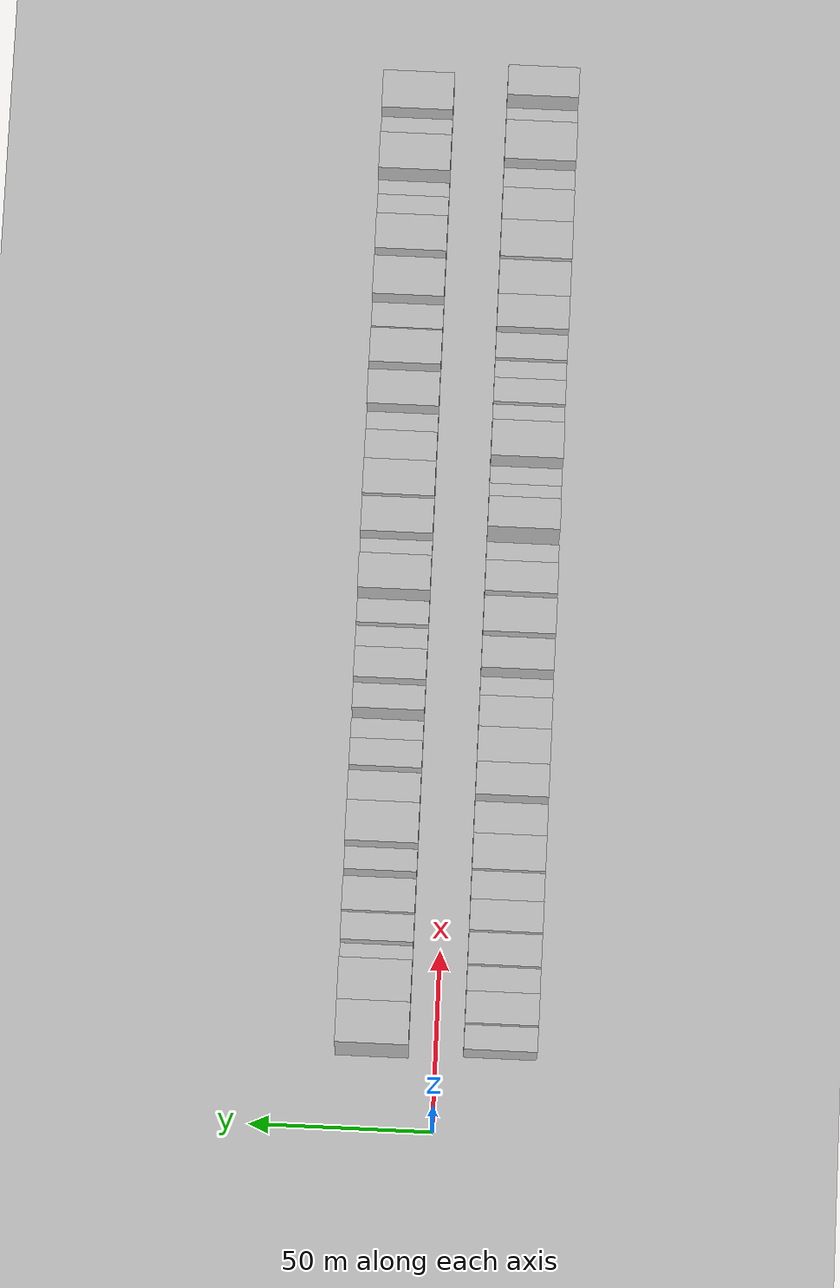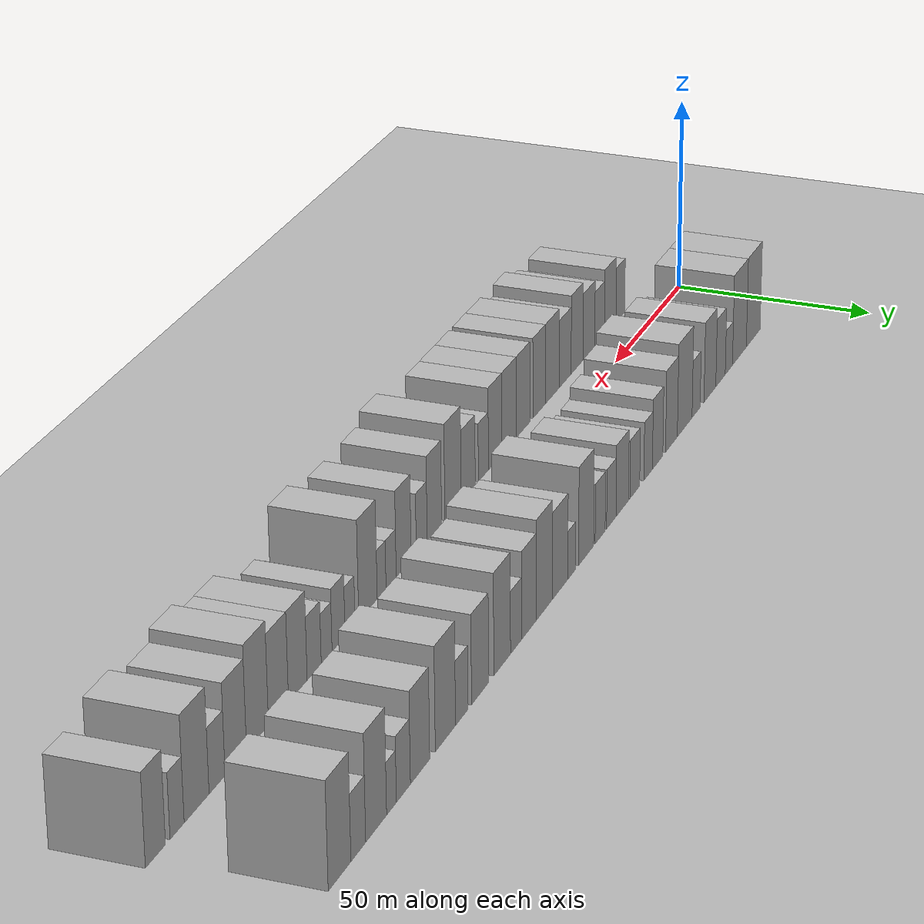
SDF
<?xml version="1.0" encoding="utf-8"?>

<sdf version="1.6">

   <world name="default">

      <gui fullscreen="0">

         <camera name="user_camera">

            <pose>-15 0 4.57585 0 0 0</pose>

            <view_controller>orbit</view_controller>

         </camera>

      </gui>

      <scene>

         <sky>

           <clouds>

             <speed>12</speed>

           </clouds>

         </sky>

         <ambient>0.4 0.4 0.4 1</ambient>

         <background>0.7 0.7 0.7 1</background>

         <shadows>1</shadows>

      </scene>

      <gravity>0 0 -9.8066</gravity>

      <magnetic_field>6e-06 2.3e-05 -4.2e-05</magnetic_field>

      <physics default="0" name="default_physics" type="ode">

         <ode>

            <solver>

               <type>quick</type>

               <iters>10</iters>

               <sor>1.0</sor>

               <use_dynamic_moi_rescaling>0</use_dynamic_moi_rescaling>

            </solver>

            <constraints>

               <cfm>0</cfm>

               <erp>0.2</erp>

               <contact_max_correcting_vel>100</contact_max_correcting_vel>

               <contact_surface_layer>0.001</contact_surface_layer>

            </constraints>

         </ode>

         <max_step_size>0.004</max_step_size>

         <real_time_factor>1</real_time_factor>

         <real_time_update_rate>250</real_time_update_rate>

      </physics>

      <light name="sun" type="directional">

         <cast_shadows>1</cast_shadows>

         <pose>0 0 10 0 0 0</pose>

         <diffuse>0.8 0.8 0.8 1</diffuse>

         <specular>0.2 0.2 0.2 1</specular>

         <attenuation>

            <range>1000</range>

            <constant>0.9</constant>

            <linear>0.01</linear>

            <quadratic>0.001</quadratic>

         </attenuation>

         <direction>-0.5 0.1 -0.9</direction>

      </light>

      <include>

         <name>ground_plane_1</name>

         <uri>model://HANNAS_ground_plane</uri>

         <pose>0 0 0  0 0 0</pose>

      </include>

      <include>

         <name>ground_plane_2</name>

         <uri>model://HANNAS_ground_plane</uri>

         <pose>100 0 0  0 0 0</pose>

      </include>

      <model name="building_1">

         <static>1</static>

         <pose frame="">25.8638 17.5000 0 0.000000 0.000000 1.570796</pose>

         <link name="link">

            <pose frame="">0 0 12.00 0 0 0</pose>

            <collision name="collision">

               <geometry>

                  <box>

                     <size>20.0000 11.7275 24.0000</size>

                  </box>

               </geometry>

               <max_contacts>10</max_contacts>

               <surface>

                  <contact>

                     <ode/>

                  </contact>

                  <bounce/>

                  <friction>

                     <torsional>

                        <ode/>

                     </torsional>

                     <ode/>

                  </friction>

               </surface>

            </collision>

            <visual name="visual">

               <cast_shadows>0</cast_shadows>

               <geometry>

                  <box>

                     <size>20.0000 11.7275 24.0000</size>

                  </box>

               </geometry>

               <material>

                  <script>

                     <uri>model://HANNAS_wall/materials/scripts</uri>

                     <uri>model://HANNAS_wall/materials/textures</uri>

                     <name>vrc/HANNAS_wall</name>

                  </script>

               </material>

            </visual>

            <self_collide>0</self_collide>

            <enable_wind>0</enable_wind>

            <kinematic>0</kinematic>

         </link>

      </model>

      <model name="building_2">

         <static>1</static>

         <pose frame="">37.4629 17.5000 0 0.000000 0.000000 1.570796</pose>

         <link name="link">

            <pose frame="">0 0 12.00 0 0 0</pose>

            <collision name="collision">

               <geometry>

                  <box>

                     <size>20.0000 11.4708 24.0000</size>

                  </box>

               </geometry>

               <max_contacts>10</max_contacts>

               <surface>

                  <contact>

                     <ode/>

                  </contact>

                  <bounce/>

                  <friction>

                     <torsional>

                        <ode/>

                     </torsional>

                     <ode/>

                  </friction>

               </surface>

            </collision>

            <visual name="visual">

               <cast_shadows>0</cast_shadows>

               <geometry>

                  <box>

                     <size>20.0000 11.4708 24.0000</size>

                  </box>

               </geometry>

               <material>

                  <script>

                     <uri>model://HANNAS_wall/materials/scripts</uri>

                     <uri>model://HANNAS_wall/materials/textures</uri>

                     <name>vrc/HANNAS_wall</name>

                  </script>

               </material>

            </visual>

            <self_collide>0</self_collide>

            <enable_wind>0</enable_wind>

            <kinematic>0</kinematic>

         </link>

      </model>

      <model name="building_3">

         <static>1</static>

         <pose frame="">46.1429 17.5000 0 0.000000 0.000000 1.570796</pose>

         <link name="link">

            <pose frame="">0 0 6.00 0 0 0</pose>

            <collision name="collision">

               <geometry>

                  <box>

                     <size>20.0000 5.8892 12.0000</size>

                  </box>

               </geometry>

               <max_contacts>10</max_contacts>

               <surface>

                  <contact>

                     <ode/>

                  </contact>

                  <bounce/>

                  <friction>

                     <torsional>

                        <ode/>

                     </torsional>

                     <ode/>

                  </friction>

               </surface>

            </collision>

            <visual name="visual">

               <cast_shadows>0</cast_shadows>

               <geometry>

                  <box>

                     <size>20.0000 5.8892 12.0000</size>

                  </box>

               </geometry>

               <material>

                  <script>

                     <uri>model://HANNAS_wall/materials/scripts</uri>

                     <uri>model://HANNAS_wall/materials/textures</uri>

                     <name>vrc/HANNAS_wall</name>

                  </script>

               </material>

            </visual>

            <self_collide>0</self_collide>

            <enable_wind>0</enable_wind>

            <kinematic>0</kinematic>

         </link>

      </model>

      <model name="building_4">

         <static>1</static>

         <pose frame="">52.8842 17.5000 0 0.000000 0.000000 1.570796</pose>

         <link name="link">

            <pose frame="">0 0 9.00 0 0 0</pose>

            <collision name="collision">

               <geometry>

                  <box>

                     <size>20.0000 7.5933 18.0000</size>

                  </box>

               </geometry>

               <max_contacts>10</max_contacts>

               <surface>

                  <contact>

                     <ode/>

                  </contact>

                  <bounce/>

                  <friction>

                     <torsional>

                        <ode/>

                     </torsional>

                     <ode/>

                  </friction>

               </surface>

            </collision>

            <visual name="visual">

               <cast_shadows>0</cast_shadows>

               <geometry>

                  <box>

                     <size>20.0000 7.5933 18.0000</size>

                  </box>

               </geometry>

               <material>

                  <script>

                     <uri>model://HANNAS_wall/materials/scripts</uri>

                     <uri>model://HANNAS_wall/materials/textures</uri>

                     <name>vrc/HANNAS_wall</name>

                  </script>

               </material>

            </visual>

            <self_collide>0</self_collide>

            <enable_wind>0</enable_wind>

            <kinematic>0</kinematic>

         </link>

      </model>

      <model name="building_5">

         <static>1</static>

         <pose frame="">61.3666 17.5000 0 0.000000 0.000000 1.570796</pose>

         <link name="link">

            <pose frame="">0 0 10.50 0 0 0</pose>

            <collision name="collision">

               <geometry>

                  <box>

                     <size>20.0000 9.3717 21.0000</size>

                  </box>

               </geometry>

               <max_contacts>10</max_contacts>

               <surface>

                  <contact>

                     <ode/>

                  </contact>

                  <bounce/>

                  <friction>

                     <torsional>

                        <ode/>

                     </torsional>

                     <ode/>

                  </friction>

               </surface>

            </collision>

            <visual name="visual">

               <cast_shadows>0</cast_shadows>

               <geometry>

                  <box>

                     <size>20.0000 9.3717 21.0000</size>

                  </box>

               </geometry>

               <material>

                  <script>

                     <uri>model://HANNAS_wall/materials/scripts</uri>

                     <uri>model://HANNAS_wall/materials/textures</uri>

                     <name>vrc/HANNAS_wall</name>

                  </script>

               </material>

            </visual>

            <self_collide>0</self_collide>

            <enable_wind>0</enable_wind>

            <kinematic>0</kinematic>

         </link>

      </model>

      <model name="building_6">

         <static>1</static>

         <pose frame="">72.1852 17.5000 0 0.000000 0.000000 1.570796</pose>

         <link name="link">

            <pose frame="">0 0 7.50 0 0 0</pose>

            <collision name="collision">

               <geometry>

                  <box>

                     <size>20.0000 6.2654 15.0000</size>

                  </box>

               </geometry>

               <max_contacts>10</max_contacts>

               <surface>

                  <contact>

                     <ode/>

                  </contact>

                  <bounce/>

                  <friction>

                     <torsional>

                        <ode/>

                     </torsional>

                     <ode/>

                  </friction>

               </surface>

            </collision>

            <visual name="visual">

               <cast_shadows>0</cast_shadows>

               <geometry>

                  <box>

                     <size>20.0000 6.2654 15.0000</size>

                  </box>

               </geometry>

               <material>

                  <script>

                     <uri>model://HANNAS_wall/materials/scripts</uri>

                     <uri>model://HANNAS_wall/materials/textures</uri>

                     <name>vrc/HANNAS_wall</name>

                  </script>

               </material>

            </visual>

            <self_collide>0</self_collide>

            <enable_wind>0</enable_wind>

            <kinematic>0</kinematic>

         </link>

      </model>

      <model name="building_7">

         <static>1</static>

         <pose frame="">80.9317 17.5000 0 0.000000 0.000000 1.570796</pose>

         <link name="link">

            <pose frame="">0 0 12.00 0 0 0</pose>

            <collision name="collision">

               <geometry>

                  <box>

                     <size>20.0000 11.2277 24.0000</size>

                  </box>

               </geometry>

               <max_contacts>10</max_contacts>

               <surface>

                  <contact>

                     <ode/>

                  </contact>

                  <bounce/>

                  <friction>

                     <torsional>

                        <ode/>

                     </torsional>

                     <ode/>

                  </friction>

               </surface>

            </collision>

            <visual name="visual">

               <cast_shadows>0</cast_shadows>

               <geometry>

                  <box>

                     <size>20.0000 11.2277 24.0000</size>

                  </box>

               </geometry>

               <material>

                  <script>

                     <uri>model://HANNAS_wall/materials/scripts</uri>

                     <uri>model://HANNAS_wall/materials/textures</uri>

                     <name>vrc/HANNAS_wall</name>

                  </script>

               </material>

            </visual>

            <self_collide>0</self_collide>

            <enable_wind>0</enable_wind>

            <kinematic>0</kinematic>

         </link>

      </model>

      <model name="building_8">

         <static>1</static>

         <pose frame="">90.9545 17.5000 0 0.000000 0.000000 1.570796</pose>

         <link name="link">

            <pose frame="">0 0 10.50 0 0 0</pose>

            <collision name="collision">

               <geometry>

                  <box>

                     <size>20.0000 8.8179 21.0000</size>

                  </box>

               </geometry>

               <max_contacts>10</max_contacts>

               <surface>

                  <contact>

                     <ode/>

                  </contact>

                  <bounce/>

                  <friction>

                     <torsional>

                        <ode/>

                     </torsional>

                     <ode/>

                  </friction>

               </surface>

            </collision>

            <visual name="visual">

               <cast_shadows>0</cast_shadows>

               <geometry>

                  <box>

                     <size>20.0000 8.8179 21.0000</size>

                  </box>

               </geometry>

               <material>

                  <script>

                     <uri>model://HANNAS_wall/materials/scripts</uri>

                     <uri>model://HANNAS_wall/materials/textures</uri>

                     <name>vrc/HANNAS_wall</name>

                  </script>

               </material>

            </visual>

            <self_collide>0</self_collide>

            <enable_wind>0</enable_wind>

            <kinematic>0</kinematic>

         </link>

      </model>

      <model name="building_9">

         <static>1</static>

         <pose frame="">101.1711 17.5000 0 0.000000 0.000000 1.570796</pose>

         <link name="link">

            <pose frame="">0 0 9.00 0 0 0</pose>

            <collision name="collision">

               <geometry>

                  <box>

                     <size>20.0000 7.6154 18.0000</size>

                  </box>

               </geometry>

               <max_contacts>10</max_contacts>

               <surface>

                  <contact>

                     <ode/>

                  </contact>

                  <bounce/>

                  <friction>

                     <torsional>

                        <ode/>

                     </torsional>

                     <ode/>

                  </friction>

               </surface>

            </collision>

            <visual name="visual">

               <cast_shadows>0</cast_shadows>

               <geometry>

                  <box>

                     <size>20.0000 7.6154 18.0000</size>

                  </box>

               </geometry>

               <material>

                  <script>

                     <uri>model://HANNAS_wall/materials/scripts</uri>

                     <uri>model://HANNAS_wall/materials/textures</uri>

                     <name>vrc/HANNAS_wall</name>

                  </script>

               </material>

            </visual>

            <self_collide>0</self_collide>

            <enable_wind>0</enable_wind>

            <kinematic>0</kinematic>

         </link>

      </model>

      <model name="building_10">

         <static>1</static>

         <pose frame="">108.0555 17.5000 0 0.000000 0.000000 1.570796</pose>

         <link name="link">

            <pose frame="">0 0 7.50 0 0 0</pose>

            <collision name="collision">

               <geometry>

                  <box>

                     <size>20.0000 6.1534 15.0000</size>

                  </box>

               </geometry>

               <max_contacts>10</max_contacts>

               <surface>

                  <contact>

                     <ode/>

                  </contact>

                  <bounce/>

                  <friction>

                     <torsional>

                        <ode/>

                     </torsional>

                     <ode/>

                  </friction>

               </surface>

            </collision>

            <visual name="visual">

               <cast_shadows>0</cast_shadows>

               <geometry>

                  <box>

                     <size>20.0000 6.1534 15.0000</size>

                  </box>

               </geometry>

               <material>

                  <script>

                     <uri>model://HANNAS_wall/materials/scripts</uri>

                     <uri>model://HANNAS_wall/materials/textures</uri>

                     <name>vrc/HANNAS_wall</name>

                  </script>

               </material>

            </visual>

            <self_collide>0</self_collide>

            <enable_wind>0</enable_wind>

            <kinematic>0</kinematic>

         </link>

      </model>

      <model name="building_11">

         <static>1</static>

         <pose frame="">117.6069 17.5000 0 0.000000 0.000000 1.570796</pose>

         <link name="link">

            <pose frame="">0 0 7.50 0 0 0</pose>

            <collision name="collision">

               <geometry>

                  <box>

                     <size>20.0000 6.9494 15.0000</size>

                  </box>

               </geometry>

               <max_contacts>10</max_contacts>

               <surface>

                  <contact>

                     <ode/>

                  </contact>

                  <bounce/>

                  <friction>

                     <torsional>

                        <ode/>

                     </torsional>

                     <ode/>

                  </friction>

               </surface>

            </collision>

            <visual name="visual">

               <cast_shadows>0</cast_shadows>

               <geometry>

                  <box>

                     <size>20.0000 6.9494 15.0000</size>

                  </box>

               </geometry>

               <material>

                  <script>

                     <uri>model://HANNAS_wall/materials/scripts</uri>

                     <uri>model://HANNAS_wall/materials/textures</uri>

                     <name>vrc/HANNAS_wall</name>

                  </script>

               </material>

            </visual>

            <self_collide>0</self_collide>

            <enable_wind>0</enable_wind>

            <kinematic>0</kinematic>

         </link>

      </model>

      <model name="building_12">

         <static>1</static>

         <pose frame="">126.3903 17.5000 0 0.000000 0.000000 1.570796</pose>

         <link name="link">

            <pose frame="">0 0 9.00 0 0 0</pose>

            <collision name="collision">

               <geometry>

                  <box>

                     <size>20.0000 8.6175 18.0000</size>

                  </box>

               </geometry>

               <max_contacts>10</max_contacts>

               <surface>

                  <contact>

                     <ode/>

                  </contact>

                  <bounce/>

                  <friction>

                     <torsional>

                        <ode/>

                     </torsional>

                     <ode/>

                  </friction>

               </surface>

            </collision>

            <visual name="visual">

               <cast_shadows>0</cast_shadows>

               <geometry>

                  <box>

                     <size>20.0000 8.6175 18.0000</size>

                  </box>

               </geometry>

               <material>

                  <script>

                     <uri>model://HANNAS_wall/materials/scripts</uri>

                     <uri>model://HANNAS_wall/materials/textures</uri>

                     <name>vrc/HANNAS_wall</name>

                  </script>

               </material>

            </visual>

            <self_collide>0</self_collide>

            <enable_wind>0</enable_wind>

            <kinematic>0</kinematic>

         </link>

      </model>

      <model name="building_13">

         <static>1</static>

         <pose frame="">133.9162 17.5000 0 0.000000 0.000000 1.570796</pose>

         <link name="link">

            <pose frame="">0 0 7.50 0 0 0</pose>

            <collision name="collision">

               <geometry>

                  <box>

                     <size>20.0000 6.4343 15.0000</size>

                  </box>

               </geometry>

               <max_contacts>10</max_contacts>

               <surface>

                  <contact>

                     <ode/>

                  </contact>

                  <bounce/>

                  <friction>

                     <torsional>

                        <ode/>

                     </torsional>

                     <ode/>

                  </friction>

               </surface>

            </collision>

            <visual name="visual">

               <cast_shadows>0</cast_shadows>

               <geometry>

                  <box>

                     <size>20.0000 6.4343 15.0000</size>

                  </box>

               </geometry>

               <material>

                  <script>

                     <uri>model://HANNAS_wall/materials/scripts</uri>

                     <uri>model://HANNAS_wall/materials/textures</uri>

                     <name>vrc/HANNAS_wall</name>

                  </script>

               </material>

            </visual>

            <self_collide>0</self_collide>

            <enable_wind>0</enable_wind>

            <kinematic>0</kinematic>

         </link>

      </model>

      <model name="building_14">

         <static>1</static>

         <pose frame="">141.4976 17.5000 0 0.000000 0.000000 1.570796</pose>

         <link name="link">

            <pose frame="">0 0 7.50 0 0 0</pose>

            <collision name="collision">

               <geometry>

                  <box>

                     <size>20.0000 6.7287 15.0000</size>

                  </box>

               </geometry>

               <max_contacts>10</max_contacts>

               <surface>

                  <contact>

                     <ode/>

                  </contact>

                  <bounce/>

                  <friction>

                     <torsional>

                        <ode/>

                     </torsional>

                     <ode/>

                  </friction>

               </surface>

            </collision>

            <visual name="visual">

               <cast_shadows>0</cast_shadows>

               <geometry>

                  <box>

                     <size>20.0000 6.7287 15.0000</size>

                  </box>

               </geometry>

               <material>

                  <script>

                     <uri>model://HANNAS_wall/materials/scripts</uri>

                     <uri>model://HANNAS_wall/materials/textures</uri>

                     <name>vrc/HANNAS_wall</name>

                  </script>

               </material>

            </visual>

            <self_collide>0</self_collide>

            <enable_wind>0</enable_wind>

            <kinematic>0</kinematic>

         </link>

      </model>

      <model name="building_15">

         <static>1</static>

         <pose frame="">150.8049 17.5000 0 0.000000 0.000000 1.570796</pose>

         <link name="link">

            <pose frame="">0 0 12.00 0 0 0</pose>

            <collision name="collision">

               <geometry>

                  <box>

                     <size>20.0000 9.8858 24.0000</size>

                  </box>

               </geometry>

               <max_contacts>10</max_contacts>

               <surface>

                  <contact>

                     <ode/>

                  </contact>

                  <bounce/>

                  <friction>

                     <torsional>

                        <ode/>

                     </torsional>

                     <ode/>

                  </friction>

               </surface>

            </collision>

            <visual name="visual">

               <cast_shadows>0</cast_shadows>

               <geometry>

                  <box>

                     <size>20.0000 9.8858 24.0000</size>

                  </box>

               </geometry>

               <material>

                  <script>

                     <uri>model://HANNAS_wall/materials/scripts</uri>

                     <uri>model://HANNAS_wall/materials/textures</uri>

                     <name>vrc/HANNAS_wall</name>

                  </script>

               </material>

            </visual>

            <self_collide>0</self_collide>

            <enable_wind>0</enable_wind>

            <kinematic>0</kinematic>

         </link>

      </model>

      <model name="building_16">

         <static>1</static>

         <pose frame="">160.2080 17.5000 0 0.000000 0.000000 1.570796</pose>

         <link name="link">

            <pose frame="">0 0 6.00 0 0 0</pose>

            <collision name="collision">

               <geometry>

                  <box>

                     <size>20.0000 4.9205 12.0000</size>

                  </box>

               </geometry>

               <max_contacts>10</max_contacts>

               <surface>

                  <contact>

                     <ode/>

                  </contact>

                  <bounce/>

                  <friction>

                     <torsional>

                        <ode/>

                     </torsional>

                     <ode/>

                  </friction>

               </surface>

            </collision>

            <visual name="visual">

               <cast_shadows>0</cast_shadows>

               <geometry>

                  <box>

                     <size>20.0000 4.9205 12.0000</size>

                  </box>

               </geometry>

               <material>

                  <script>

                     <uri>model://HANNAS_wall/materials/scripts</uri>

                     <uri>model://HANNAS_wall/materials/textures</uri>

                     <name>vrc/HANNAS_wall</name>

                  </script>

               </material>

            </visual>

            <self_collide>0</self_collide>

            <enable_wind>0</enable_wind>

            <kinematic>0</kinematic>

         </link>

      </model>

      <model name="building_17">

         <static>1</static>

         <pose frame="">167.6149 17.5000 0 0.000000 0.000000 1.570796</pose>

         <link name="link">

            <pose frame="">0 0 10.50 0 0 0</pose>

            <collision name="collision">

               <geometry>

                  <box>

                     <size>20.0000 9.8932 21.0000</size>

                  </box>

               </geometry>

               <max_contacts>10</max_contacts>

               <surface>

                  <contact>

                     <ode/>

                  </contact>

                  <bounce/>

                  <friction>

                     <torsional>

                        <ode/>

                     </torsional>

                     <ode/>

                  </friction>

               </surface>

            </collision>

            <visual name="visual">

               <cast_shadows>0</cast_shadows>

               <geometry>

                  <box>

                     <size>20.0000 9.8932 21.0000</size>

                  </box>

               </geometry>

               <material>

                  <script>

                     <uri>model://HANNAS_wall/materials/scripts</uri>

                     <uri>model://HANNAS_wall/materials/textures</uri>

                     <name>vrc/HANNAS_wall</name>

                  </script>

               </material>

            </visual>

            <self_collide>0</self_collide>

            <enable_wind>0</enable_wind>

            <kinematic>0</kinematic>

         </link>

      </model>

      <model name="building_18">

         <static>1</static>

         <pose frame="">177.5266 17.5000 0 0.000000 0.000000 1.570796</pose>

         <link name="link">

            <pose frame="">0 0 12.00 0 0 0</pose>

            <collision name="collision">

               <geometry>

                  <box>

                     <size>20.0000 9.9304 24.0000</size>

                  </box>

               </geometry>

               <max_contacts>10</max_contacts>

               <surface>

                  <contact>

                     <ode/>

                  </contact>

                  <bounce/>

                  <friction>

                     <torsional>

                        <ode/>

                     </torsional>

                     <ode/>

                  </friction>

               </surface>

            </collision>

            <visual name="visual">

               <cast_shadows>0</cast_shadows>

               <geometry>

                  <box>

                     <size>20.0000 9.9304 24.0000</size>

                  </box>

               </geometry>

               <material>

                  <script>

                     <uri>model://HANNAS_wall/materials/scripts</uri>

                     <uri>model://HANNAS_wall/materials/textures</uri>

                     <name>vrc/HANNAS_wall</name>

                  </script>

               </material>

            </visual>

            <self_collide>0</self_collide>

            <enable_wind>0</enable_wind>

            <kinematic>0</kinematic>

         </link>

      </model>

      <model name="building_19">

         <static>1</static>

         <pose frame="">186.9951 17.5000 0 0.000000 0.000000 1.570796</pose>

         <link name="link">

            <pose frame="">0 0 10.50 0 0 0</pose>

            <collision name="collision">

               <geometry>

                  <box>

                     <size>20.0000 9.0066 21.0000</size>

                  </box>

               </geometry>

               <max_contacts>10</max_contacts>

               <surface>

                  <contact>

                     <ode/>

                  </contact>

                  <bounce/>

                  <friction>

                     <torsional>

                        <ode/>

                     </torsional>

                     <ode/>

                  </friction>

               </surface>

            </collision>

            <visual name="visual">

               <cast_shadows>0</cast_shadows>

               <geometry>

                  <box>

                     <size>20.0000 9.0066 21.0000</size>

                  </box>

               </geometry>

               <material>

                  <script>

                     <uri>model://HANNAS_wall/materials/scripts</uri>

                     <uri>model://HANNAS_wall/materials/textures</uri>

                     <name>vrc/HANNAS_wall</name>

                  </script>

               </material>

            </visual>

            <self_collide>0</self_collide>

            <enable_wind>0</enable_wind>

            <kinematic>0</kinematic>

         </link>

      </model>

      <model name="building_20">

         <static>1</static>

         <pose frame="">194.8216 17.5000 0 0.000000 0.000000 1.570796</pose>

         <link name="link">

            <pose frame="">0 0 7.50 0 0 0</pose>

            <collision name="collision">

               <geometry>

                  <box>

                     <size>20.0000 6.6463 15.0000</size>

                  </box>

               </geometry>

               <max_contacts>10</max_contacts>

               <surface>

                  <contact>

                     <ode/>

                  </contact>

                  <bounce/>

                  <friction>

                     <torsional>

                        <ode/>

                     </torsional>

                     <ode/>

                  </friction>

               </surface>

            </collision>

            <visual name="visual">

               <cast_shadows>0</cast_shadows>

               <geometry>

                  <box>

                     <size>20.0000 6.6463 15.0000</size>

                  </box>

               </geometry>

               <material>

                  <script>

                     <uri>model://HANNAS_wall/materials/scripts</uri>

                     <uri>model://HANNAS_wall/materials/textures</uri>

                     <name>vrc/HANNAS_wall</name>

                  </script>

               </material>

            </visual>

            <self_collide>0</self_collide>

            <enable_wind>0</enable_wind>

            <kinematic>0</kinematic>

         </link>

      </model>

      <model name="building_21">

         <static>1</static>

         <pose frame="">203.0337 17.5000 0 0.000000 0.000000 1.570796</pose>

         <link name="link">

            <pose frame="">0 0 12.00 0 0 0</pose>

            <collision name="collision">

               <geometry>

                  <box>

                     <size>20.0000 9.7779 24.0000</size>

                  </box>

               </geometry>

               <max_contacts>10</max_contacts>

               <surface>

                  <contact>

                     <ode/>

                  </contact>

                  <bounce/>

                  <friction>

                     <torsional>

                        <ode/>

                     </torsional>

                     <ode/>

                  </friction>

               </surface>

            </collision>

            <visual name="visual">

               <cast_shadows>0</cast_shadows>

               <geometry>

                  <box>

                     <size>20.0000 9.7779 24.0000</size>

                  </box>

               </geometry>

               <material>

                  <script>

                     <uri>model://HANNAS_wall/materials/scripts</uri>

                     <uri>model://HANNAS_wall/materials/textures</uri>

                     <name>vrc/HANNAS_wall</name>

                  </script>

               </material>

            </visual>

            <self_collide>0</self_collide>

            <enable_wind>0</enable_wind>

            <kinematic>0</kinematic>

         </link>

      </model>

      <model name="building_22">

         <static>1</static>

         <pose frame="">215.8172 17.5000 0 0.000000 0.000000 1.570796</pose>

         <link name="link">

            <pose frame="">0 0 10.50 0 0 0</pose>

            <collision name="collision">

               <geometry>

                  <box>

                     <size>20.0000 9.7892 21.0000</size>

                  </box>

               </geometry>

               <max_contacts>10</max_contacts>

               <surface>

                  <contact>

                     <ode/>

                  </contact>

                  <bounce/>

                  <friction>

                     <torsional>

                        <ode/>

                     </torsional>

                     <ode/>

                  </friction>

               </surface>

            </collision>

            <visual name="visual">

               <cast_shadows>0</cast_shadows>

               <geometry>

                  <box>

                     <size>20.0000 9.7892 21.0000</size>

                  </box>

               </geometry>

               <material>

                  <script>

                     <uri>model://HANNAS_wall/materials/scripts</uri>

                     <uri>model://HANNAS_wall/materials/textures</uri>

                     <name>vrc/HANNAS_wall</name>

                  </script>

               </material>

            </visual>

            <self_collide>0</self_collide>

            <enable_wind>0</enable_wind>

            <kinematic>0</kinematic>

         </link>

      </model>

      <model name="building_23">

         <static>1</static>

         <pose frame="">226.1819 17.5000 0 0.000000 0.000000 1.570796</pose>

         <link name="link">

            <pose frame="">0 0 7.50 0 0 0</pose>

            <collision name="collision">

               <geometry>

                  <box>

                     <size>20.0000 6.9402 15.0000</size>

                  </box>

               </geometry>

               <max_contacts>10</max_contacts>

               <surface>

                  <contact>

                     <ode/>

                  </contact>

                  <bounce/>

                  <friction>

                     <torsional>

                        <ode/>

                     </torsional>

                     <ode/>

                  </friction>

               </surface>

            </collision>

            <visual name="visual">

               <cast_shadows>0</cast_shadows>

               <geometry>

                  <box>

                     <size>20.0000 6.9402 15.0000</size>

                  </box>

               </geometry>

               <material>

                  <script>

                     <uri>model://HANNAS_wall/materials/scripts</uri>

                     <uri>model://HANNAS_wall/materials/textures</uri>

                     <name>vrc/HANNAS_wall</name>

                  </script>

               </material>

            </visual>

            <self_collide>0</self_collide>

            <enable_wind>0</enable_wind>

            <kinematic>0</kinematic>

         </link>

      </model>

      <model name="building_24">

         <static>1</static>

         <pose frame="">235.1652 17.5000 0 0.000000 0.000000 1.570796</pose>

         <link name="link">

            <pose frame="">0 0 12.00 0 0 0</pose>

            <collision name="collision">

               <geometry>

                  <box>

                     <size>20.0000 11.0265 24.0000</size>

                  </box>

               </geometry>

               <max_contacts>10</max_contacts>

               <surface>

                  <contact>

                     <ode/>

                  </contact>

                  <bounce/>

                  <friction>

                     <torsional>

                        <ode/>

                     </torsional>

                     <ode/>

                  </friction>

               </surface>

            </collision>

            <visual name="visual">

               <cast_shadows>0</cast_shadows>

               <geometry>

                  <box>

                     <size>20.0000 11.0265 24.0000</size>

                  </box>

               </geometry>

               <material>

                  <script>

                     <uri>model://HANNAS_wall/materials/scripts</uri>

                     <uri>model://HANNAS_wall/materials/textures</uri>

                     <name>vrc/HANNAS_wall</name>

                  </script>

               </material>

            </visual>

            <self_collide>0</self_collide>

            <enable_wind>0</enable_wind>

            <kinematic>0</kinematic>

         </link>

      </model>

      <model name="building_25">

         <static>1</static>

         <pose frame="">248.7692 17.5000 0 0.000000 0.000000 1.570796</pose>

         <link name="link">

            <pose frame="">0 0 10.50 0 0 0</pose>

            <collision name="collision">

               <geometry>

                  <box>

                     <size>20.0000 10.1814 21.0000</size>

                  </box>

               </geometry>

               <max_contacts>10</max_contacts>

               <surface>

                  <contact>

                     <ode/>

                  </contact>

                  <bounce/>

                  <friction>

                     <torsional>

                        <ode/>

                     </torsional>

                     <ode/>

                  </friction>

               </surface>

            </collision>

            <visual name="visual">

               <cast_shadows>0</cast_shadows>

               <geometry>

                  <box>

                     <size>20.0000 10.1814 21.0000</size>

                  </box>

               </geometry>

               <material>

                  <script>

                     <uri>model://HANNAS_wall/materials/scripts</uri>

                     <uri>model://HANNAS_wall/materials/textures</uri>

                     <name>vrc/HANNAS_wall</name>

                  </script>

               </material>

            </visual>

            <self_collide>0</self_collide>

            <enable_wind>0</enable_wind>

            <kinematic>0</kinematic>

         </link>

      </model>

      <model name="building_26">

         <static>1</static>

         <pose frame="">257.4827 17.5000 0 0.000000 0.000000 1.570796</pose>

         <link name="link">

            <pose frame="">0 0 7.50 0 0 0</pose>

            <collision name="collision">

               <geometry>

                  <box>

                     <size>20.0000 7.2456 15.0000</size>

                  </box>

               </geometry>

               <max_contacts>10</max_contacts>

               <surface>

                  <contact>

                     <ode/>

                  </contact>

                  <bounce/>

                  <friction>

                     <torsional>

                        <ode/>

                     </torsional>

                     <ode/>

                  </friction>

               </surface>

            </collision>

            <visual name="visual">

               <cast_shadows>0</cast_shadows>

               <geometry>

                  <box>

                     <size>20.0000 7.2456 15.0000</size>

                  </box>

               </geometry>

               <material>

                  <script>

                     <uri>model://HANNAS_wall/materials/scripts</uri>

                     <uri>model://HANNAS_wall/materials/textures</uri>

                     <name>vrc/HANNAS_wall</name>

                  </script>

               </material>

            </visual>

            <self_collide>0</self_collide>

            <enable_wind>0</enable_wind>

            <kinematic>0</kinematic>

         </link>

      </model>

      <model name="building_27">

         <static>1</static>

         <pose frame="">263.6017 17.5000 0 0.000000 0.000000 1.570796</pose>

         <link name="link">

            <pose frame="">0 0 6.00 0 0 0</pose>

            <collision name="collision">

               <geometry>

                  <box>

                     <size>20.0000 4.9924 12.0000</size>

                  </box>

               </geometry>

               <max_contacts>10</max_contacts>

               <surface>

                  <contact>

                     <ode/>

                  </contact>

                  <bounce/>

                  <friction>

                     <torsional>

                        <ode/>

                     </torsional>

                     <ode/>

                  </friction>

               </surface>

            </collision>

            <visual name="visual">

               <cast_shadows>0</cast_shadows>

               <geometry>

                  <box>

                     <size>20.0000 4.9924 12.0000</size>

                  </box>

               </geometry>

               <material>

                  <script>

                     <uri>model://HANNAS_wall/materials/scripts</uri>

                     <uri>model://HANNAS_wall/materials/textures</uri>

                     <name>vrc/HANNAS_wall</name>

                  </script>

               </material>

            </visual>

            <self_collide>0</self_collide>

            <enable_wind>0</enable_wind>

            <kinematic>0</kinematic>

         </link>

      </model>

      <model name="building_28">

         <static>1</static>

         <pose frame="">271.3179 17.5000 0 0.000000 0.000000 1.570796</pose>

         <link name="link">

            <pose frame="">0 0 12.00 0 0 0</pose>

            <collision name="collision">

               <geometry>

                  <box>

                     <size>20.0000 10.4401 24.0000</size>

                  </box>

               </geometry>

               <max_contacts>10</max_contacts>

               <surface>

                  <contact>

                     <ode/>

                  </contact>

                  <bounce/>

                  <friction>

                     <torsional>

                        <ode/>

                     </torsional>

                     <ode/>

                  </friction>

               </surface>

            </collision>

            <visual name="visual">

               <cast_shadows>0</cast_shadows>

               <geometry>

                  <box>

                     <size>20.0000 10.4401 24.0000</size>

                  </box>

               </geometry>

               <material>

                  <script>

                     <uri>model://HANNAS_wall/materials/scripts</uri>

                     <uri>model://HANNAS_wall/materials/textures</uri>

                     <name>vrc/HANNAS_wall</name>

                  </script>

               </material>

            </visual>

            <self_collide>0</self_collide>

            <enable_wind>0</enable_wind>

            <kinematic>0</kinematic>

         </link>

      </model>

      <model name="building_29">

         <static>1</static>

         <pose frame="">280.1564 17.5000 0 0.000000 0.000000 1.570796</pose>

         <link name="link">

            <pose frame="">0 0 7.50 0 0 0</pose>

            <collision name="collision">

               <geometry>

                  <box>

                     <size>20.0000 7.2369 15.0000</size>

                  </box>

               </geometry>

               <max_contacts>10</max_contacts>

               <surface>

                  <contact>

                     <ode/>

                  </contact>

                  <bounce/>

                  <friction>

                     <torsional>

                        <ode/>

                     </torsional>

                     <ode/>

                  </friction>

               </surface>

            </collision>

            <visual name="visual">

               <cast_shadows>0</cast_shadows>

               <geometry>

                  <box>

                     <size>20.0000 7.2369 15.0000</size>

                  </box>

               </geometry>

               <material>

                  <script>

                     <uri>model://HANNAS_wall/materials/scripts</uri>

                     <uri>model://HANNAS_wall/materials/textures</uri>

                     <name>vrc/HANNAS_wall</name>

                  </script>

               </material>

            </visual>

            <self_collide>0</self_collide>

            <enable_wind>0</enable_wind>

            <kinematic>0</kinematic>

         </link>

      </model>

      <model name="building_30">

         <static>1</static>

         <pose frame="">289.2104 17.5000 0 0.000000 0.000000 1.570796</pose>

         <link name="link">

            <pose frame="">0 0 12.00 0 0 0</pose>

            <collision name="collision">

               <geometry>

                  <box>

                     <size>20.0000 10.8711 24.0000</size>

                  </box>

               </geometry>

               <max_contacts>10</max_contacts>

               <surface>

                  <contact>

                     <ode/>

                  </contact>

                  <bounce/>

                  <friction>

                     <torsional>

                        <ode/>

                     </torsional>

                     <ode/>

                  </friction>

               </surface>

            </collision>

            <visual name="visual">

               <cast_shadows>0</cast_shadows>

               <geometry>

                  <box>

                     <size>20.0000 10.8711 24.0000</size>

                  </box>

               </geometry>

               <material>

                  <script>

                     <uri>model://HANNAS_wall/materials/scripts</uri>

                     <uri>model://HANNAS_wall/materials/textures</uri>

                     <name>vrc/HANNAS_wall</name>

                  </script>

               </material>

            </visual>

            <self_collide>0</self_collide>

            <enable_wind>0</enable_wind>

            <kinematic>0</kinematic>

         </link>

      </model>

      <model name="building_31">

         <static>1</static>

         <pose frame="">24.3830 -17.5000 0 0.000000 0.000000 1.570796</pose>

         <link name="link">

            <pose frame="">0 0 7.50 0 0 0</pose>

            <collision name="collision">

               <geometry>

                  <box>

                     <size>20.0000 6.7660 15.0000</size>

                  </box>

               </geometry>

               <max_contacts>10</max_contacts>

               <surface>

                  <contact>

                     <ode/>

                  </contact>

                  <bounce/>

                  <friction>

                     <torsional>

                        <ode/>

                     </torsional>

                     <ode/>

                  </friction>

               </surface>

            </collision>

            <visual name="visual">

               <cast_shadows>0</cast_shadows>

               <geometry>

                  <box>

                     <size>20.0000 6.7660 15.0000</size>

                  </box>

               </geometry>

               <material>

                  <script>

                     <uri>model://HANNAS_wall/materials/scripts</uri>

                     <uri>model://HANNAS_wall/materials/textures</uri>

                     <name>vrc/HANNAS_wall</name>

                  </script>

               </material>

            </visual>

            <self_collide>0</self_collide>

            <enable_wind>0</enable_wind>

            <kinematic>0</kinematic>

         </link>

      </model>

      <model name="building_32">

         <static>1</static>

         <pose frame="">32.1671 -17.5000 0 0.000000 0.000000 1.570796</pose>

         <link name="link">

            <pose frame="">0 0 9.00 0 0 0</pose>

            <collision name="collision">

               <geometry>

                  <box>

                     <size>20.0000 8.8020 18.0000</size>

                  </box>

               </geometry>

               <max_contacts>10</max_contacts>

               <surface>

                  <contact>

                     <ode/>

                  </contact>

                  <bounce/>

                  <friction>

                     <torsional>

                        <ode/>

                     </torsional>

                     <ode/>

                  </friction>

               </surface>

            </collision>

            <visual name="visual">

               <cast_shadows>0</cast_shadows>

               <geometry>

                  <box>

                     <size>20.0000 8.8020 18.0000</size>

                  </box>

               </geometry>

               <material>

                  <script>

                     <uri>model://HANNAS_wall/materials/scripts</uri>

                     <uri>model://HANNAS_wall/materials/textures</uri>

                     <name>vrc/HANNAS_wall</name>

                  </script>

               </material>

            </visual>

            <self_collide>0</self_collide>

            <enable_wind>0</enable_wind>

            <kinematic>0</kinematic>

         </link>

      </model>

      <model name="building_33">

         <static>1</static>

         <pose frame="">40.2377 -17.5000 0 0.000000 0.000000 1.570796</pose>

         <link name="link">

            <pose frame="">0 0 7.50 0 0 0</pose>

            <collision name="collision">

               <geometry>

                  <box>

                     <size>20.0000 7.3393 15.0000</size>

                  </box>

               </geometry>

               <max_contacts>10</max_contacts>

               <surface>

                  <contact>

                     <ode/>

                  </contact>

                  <bounce/>

                  <friction>

                     <torsional>

                        <ode/>

                     </torsional>

                     <ode/>

                  </friction>

               </surface>

            </collision>

            <visual name="visual">

               <cast_shadows>0</cast_shadows>

               <geometry>

                  <box>

                     <size>20.0000 7.3393 15.0000</size>

                  </box>

               </geometry>

               <material>

                  <script>

                     <uri>model://HANNAS_wall/materials/scripts</uri>

                     <uri>model://HANNAS_wall/materials/textures</uri>

                     <name>vrc/HANNAS_wall</name>

                  </script>

               </material>

            </visual>

            <self_collide>0</self_collide>

            <enable_wind>0</enable_wind>

            <kinematic>0</kinematic>

         </link>

      </model>

      <model name="building_34">

         <static>1</static>

         <pose frame="">48.3434 -17.5000 0 0.000000 0.000000 1.570796</pose>

         <link name="link">

            <pose frame="">0 0 9.00 0 0 0</pose>

            <collision name="collision">

               <geometry>

                  <box>

                     <size>20.0000 8.8722 18.0000</size>

                  </box>

               </geometry>

               <max_contacts>10</max_contacts>

               <surface>

                  <contact>

                     <ode/>

                  </contact>

                  <bounce/>

                  <friction>

                     <torsional>

                        <ode/>

                     </torsional>

                     <ode/>

                  </friction>

               </surface>

            </collision>

            <visual name="visual">

               <cast_shadows>0</cast_shadows>

               <geometry>

                  <box>

                     <size>20.0000 8.8722 18.0000</size>

                  </box>

               </geometry>

               <material>

                  <script>

                     <uri>model://HANNAS_wall/materials/scripts</uri>

                     <uri>model://HANNAS_wall/materials/textures</uri>

                     <name>vrc/HANNAS_wall</name>

                  </script>

               </material>

            </visual>

            <self_collide>0</self_collide>

            <enable_wind>0</enable_wind>

            <kinematic>0</kinematic>

         </link>

      </model>

      <model name="building_35">

         <static>1</static>

         <pose frame="">57.0564 -17.5000 0 0.000000 0.000000 1.570796</pose>

         <link name="link">

            <pose frame="">0 0 10.50 0 0 0</pose>

            <collision name="collision">

               <geometry>

                  <box>

                     <size>20.0000 8.5538 21.0000</size>

                  </box>

               </geometry>

               <max_contacts>10</max_contacts>

               <surface>

                  <contact>

                     <ode/>

                  </contact>

                  <bounce/>

                  <friction>

                     <torsional>

                        <ode/>

                     </torsional>

                     <ode/>

                  </friction>

               </surface>

            </collision>

            <visual name="visual">

               <cast_shadows>0</cast_shadows>

               <geometry>

                  <box>

                     <size>20.0000 8.5538 21.0000</size>

                  </box>

               </geometry>

               <material>

                  <script>

                     <uri>model://HANNAS_wall/materials/scripts</uri>

                     <uri>model://HANNAS_wall/materials/textures</uri>

                     <name>vrc/HANNAS_wall</name>

                  </script>

               </material>

            </visual>

            <self_collide>0</self_collide>

            <enable_wind>0</enable_wind>

            <kinematic>0</kinematic>

         </link>

      </model>

      <model name="building_36">

         <static>1</static>

         <pose frame="">65.5148 -17.5000 0 0.000000 0.000000 1.570796</pose>

         <link name="link">

            <pose frame="">0 0 9.00 0 0 0</pose>

            <collision name="collision">

               <geometry>

                  <box>

                     <size>20.0000 8.3629 18.0000</size>

                  </box>

               </geometry>

               <max_contacts>10</max_contacts>

               <surface>

                  <contact>

                     <ode/>

                  </contact>

                  <bounce/>

                  <friction>

                     <torsional>

                        <ode/>

                     </torsional>

                     <ode/>

                  </friction>

               </surface>

            </collision>

            <visual name="visual">

               <cast_shadows>0</cast_shadows>

               <geometry>

                  <box>

                     <size>20.0000 8.3629 18.0000</size>

                  </box>

               </geometry>

               <material>

                  <script>

                     <uri>model://HANNAS_wall/materials/scripts</uri>

                     <uri>model://HANNAS_wall/materials/textures</uri>

                     <name>vrc/HANNAS_wall</name>

                  </script>

               </material>

            </visual>

            <self_collide>0</self_collide>

            <enable_wind>0</enable_wind>

            <kinematic>0</kinematic>

         </link>

      </model>

      <model name="building_37">

         <static>1</static>

         <pose frame="">74.6277 -17.5000 0 0.000000 0.000000 1.570796</pose>

         <link name="link">

            <pose frame="">0 0 10.50 0 0 0</pose>

            <collision name="collision">

               <geometry>

                  <box>

                     <size>20.0000 9.8629 21.0000</size>

                  </box>

               </geometry>

               <max_contacts>10</max_contacts>

               <surface>

                  <contact>

                     <ode/>

                  </contact>

                  <bounce/>

                  <friction>

                     <torsional>

                        <ode/>

                     </torsional>

                     <ode/>

                  </friction>

               </surface>

            </collision>

            <visual name="visual">

               <cast_shadows>0</cast_shadows>

               <geometry>

                  <box>

                     <size>20.0000 9.8629 21.0000</size>

                  </box>

               </geometry>

               <material>

                  <script>

                     <uri>model://HANNAS_wall/materials/scripts</uri>

                     <uri>model://HANNAS_wall/materials/textures</uri>

                     <name>vrc/HANNAS_wall</name>

                  </script>

               </material>

            </visual>

            <self_collide>0</self_collide>

            <enable_wind>0</enable_wind>

            <kinematic>0</kinematic>

         </link>

      </model>

      <model name="building_38">

         <static>1</static>

         <pose frame="">83.9404 -17.5000 0 0.000000 0.000000 1.570796</pose>

         <link name="link">

            <pose frame="">0 0 10.50 0 0 0</pose>

            <collision name="collision">

               <geometry>

                  <box>

                     <size>20.0000 8.7625 21.0000</size>

                  </box>

               </geometry>

               <max_contacts>10</max_contacts>

               <surface>

                  <contact>

                     <ode/>

                  </contact>

                  <bounce/>

                  <friction>

                     <torsional>

                        <ode/>

                     </torsional>

                     <ode/>

                  </friction>

               </surface>

            </collision>

            <visual name="visual">

               <cast_shadows>0</cast_shadows>

               <geometry>

                  <box>

                     <size>20.0000 8.7625 21.0000</size>

                  </box>

               </geometry>

               <material>

                  <script>

                     <uri>model://HANNAS_wall/materials/scripts</uri>

                     <uri>model://HANNAS_wall/materials/textures</uri>

                     <name>vrc/HANNAS_wall</name>

                  </script>

               </material>

            </visual>

            <self_collide>0</self_collide>

            <enable_wind>0</enable_wind>

            <kinematic>0</kinematic>

         </link>

      </model>

      <model name="building_39">

         <static>1</static>

         <pose frame="">94.8983 -17.5000 0 0.000000 0.000000 1.570796</pose>

         <link name="link">

            <pose frame="">0 0 10.50 0 0 0</pose>

            <collision name="collision">

               <geometry>

                  <box>

                     <size>20.0000 9.1533 21.0000</size>

                  </box>

               </geometry>

               <max_contacts>10</max_contacts>

               <surface>

                  <contact>

                     <ode/>

                  </contact>

                  <bounce/>

                  <friction>

                     <torsional>

                        <ode/>

                     </torsional>

                     <ode/>

                  </friction>

               </surface>

            </collision>

            <visual name="visual">

               <cast_shadows>0</cast_shadows>

               <geometry>

                  <box>

                     <size>20.0000 9.1533 21.0000</size>

                  </box>

               </geometry>

               <material>

                  <script>

                     <uri>model://HANNAS_wall/materials/scripts</uri>

                     <uri>model://HANNAS_wall/materials/textures</uri>

                     <name>vrc/HANNAS_wall</name>

                  </script>

               </material>

            </visual>

            <self_collide>0</self_collide>

            <enable_wind>0</enable_wind>

            <kinematic>0</kinematic>

         </link>

      </model>

      <model name="building_40">

         <static>1</static>

         <pose frame="">104.3553 -17.5000 0 0.000000 0.000000 1.570796</pose>

         <link name="link">

            <pose frame="">0 0 10.50 0 0 0</pose>

            <collision name="collision">

               <geometry>

                  <box>

                     <size>20.0000 9.7607 21.0000</size>

                  </box>

               </geometry>

               <max_contacts>10</max_contacts>

               <surface>

                  <contact>

                     <ode/>

                  </contact>

                  <bounce/>

                  <friction>

                     <torsional>

                        <ode/>

                     </torsional>

                     <ode/>

                  </friction>

               </surface>

            </collision>

            <visual name="visual">

               <cast_shadows>0</cast_shadows>

               <geometry>

                  <box>

                     <size>20.0000 9.7607 21.0000</size>

                  </box>

               </geometry>

               <material>

                  <script>

                     <uri>model://HANNAS_wall/materials/scripts</uri>

                     <uri>model://HANNAS_wall/materials/textures</uri>

                     <name>vrc/HANNAS_wall</name>

                  </script>

               </material>

            </visual>

            <self_collide>0</self_collide>

            <enable_wind>0</enable_wind>

            <kinematic>0</kinematic>

         </link>

      </model>

      <model name="building_41">

         <static>1</static>

         <pose frame="">113.5725 -17.5000 0 0.000000 0.000000 1.570796</pose>

         <link name="link">

            <pose frame="">0 0 10.50 0 0 0</pose>

            <collision name="collision">

               <geometry>

                  <box>

                     <size>20.0000 8.6738 21.0000</size>

                  </box>

               </geometry>

               <max_contacts>10</max_contacts>

               <surface>

                  <contact>

                     <ode/>

                  </contact>

                  <bounce/>

                  <friction>

                     <torsional>

                        <ode/>

                     </torsional>

                     <ode/>

                  </friction>

               </surface>

            </collision>

            <visual name="visual">

               <cast_shadows>0</cast_shadows>

               <geometry>

                  <box>

                     <size>20.0000 8.6738 21.0000</size>

                  </box>

               </geometry>

               <material>

                  <script>

                     <uri>model://HANNAS_wall/materials/scripts</uri>

                     <uri>model://HANNAS_wall/materials/textures</uri>

                     <name>vrc/HANNAS_wall</name>

                  </script>

               </material>

            </visual>

            <self_collide>0</self_collide>

            <enable_wind>0</enable_wind>

            <kinematic>0</kinematic>

         </link>

      </model>

      <model name="building_42">

         <static>1</static>

         <pose frame="">121.1472 -17.5000 0 0.000000 0.000000 1.570796</pose>

         <link name="link">

            <pose frame="">0 0 7.50 0 0 0</pose>

            <collision name="collision">

               <geometry>

                  <box>

                     <size>20.0000 6.4755 15.0000</size>

                  </box>

               </geometry>

               <max_contacts>10</max_contacts>

               <surface>

                  <contact>

                     <ode/>

                  </contact>

                  <bounce/>

                  <friction>

                     <torsional>

                        <ode/>

                     </torsional>

                     <ode/>

                  </friction>

               </surface>

            </collision>

            <visual name="visual">

               <cast_shadows>0</cast_shadows>

               <geometry>

                  <box>

                     <size>20.0000 6.4755 15.0000</size>

                  </box>

               </geometry>

               <material>

                  <script>

                     <uri>model://HANNAS_wall/materials/scripts</uri>

                     <uri>model://HANNAS_wall/materials/textures</uri>

                     <name>vrc/HANNAS_wall</name>

                  </script>

               </material>

            </visual>

            <self_collide>0</self_collide>

            <enable_wind>0</enable_wind>

            <kinematic>0</kinematic>

         </link>

      </model>

      <model name="building_43">

         <static>1</static>

         <pose frame="">130.8215 -17.5000 0 0.000000 0.000000 1.570796</pose>

         <link name="link">

            <pose frame="">0 0 9.00 0 0 0</pose>

            <collision name="collision">

               <geometry>

                  <box>

                     <size>20.0000 8.8731 18.0000</size>

                  </box>

               </geometry>

               <max_contacts>10</max_contacts>

               <surface>

                  <contact>

                     <ode/>

                  </contact>

                  <bounce/>

                  <friction>

                     <torsional>

                        <ode/>

                     </torsional>

                     <ode/>

                  </friction>

               </surface>

            </collision>

            <visual name="visual">

               <cast_shadows>0</cast_shadows>

               <geometry>

                  <box>

                     <size>20.0000 8.8731 18.0000</size>

                  </box>

               </geometry>

               <material>

                  <script>

                     <uri>model://HANNAS_wall/materials/scripts</uri>

                     <uri>model://HANNAS_wall/materials/textures</uri>

                     <name>vrc/HANNAS_wall</name>

                  </script>

               </material>

            </visual>

            <self_collide>0</self_collide>

            <enable_wind>0</enable_wind>

            <kinematic>0</kinematic>

         </link>

      </model>

      <model name="building_44">

         <static>1</static>

         <pose frame="">140.2786 -17.5000 0 0.000000 0.000000 1.570796</pose>

         <link name="link">

            <pose frame="">0 0 12.00 0 0 0</pose>

            <collision name="collision">

               <geometry>

                  <box>

                     <size>20.0000 10.0412 24.0000</size>

                  </box>

               </geometry>

               <max_contacts>10</max_contacts>

               <surface>

                  <contact>

                     <ode/>

                  </contact>

                  <bounce/>

                  <friction>

                     <torsional>

                        <ode/>

                     </torsional>

                     <ode/>

                  </friction>

               </surface>

            </collision>

            <visual name="visual">

               <cast_shadows>0</cast_shadows>

               <geometry>

                  <box>

                     <size>20.0000 10.0412 24.0000</size>

                  </box>

               </geometry>

               <material>

                  <script>

                     <uri>model://HANNAS_wall/materials/scripts</uri>

                     <uri>model://HANNAS_wall/materials/textures</uri>

                     <name>vrc/HANNAS_wall</name>

                  </script>

               </material>

            </visual>

            <self_collide>0</self_collide>

            <enable_wind>0</enable_wind>

            <kinematic>0</kinematic>

         </link>

      </model>

      <model name="building_45">

         <static>1</static>

         <pose frame="">151.6497 -17.5000 0 0.000000 0.000000 1.570796</pose>

         <link name="link">

            <pose frame="">0 0 10.50 0 0 0</pose>

            <collision name="collision">

               <geometry>

                  <box>

                     <size>20.0000 8.7010 21.0000</size>

                  </box>

               </geometry>

               <max_contacts>10</max_contacts>

               <surface>

                  <contact>

                     <ode/>

                  </contact>

                  <bounce/>

                  <friction>

                     <torsional>

                        <ode/>

                     </torsional>

                     <ode/>

                  </friction>

               </surface>

            </collision>

            <visual name="visual">

               <cast_shadows>0</cast_shadows>

               <geometry>

                  <box>

                     <size>20.0000 8.7010 21.0000</size>

                  </box>

               </geometry>

               <material>

                  <script>

                     <uri>model://HANNAS_wall/materials/scripts</uri>

                     <uri>model://HANNAS_wall/materials/textures</uri>

                     <name>vrc/HANNAS_wall</name>

                  </script>

               </material>

            </visual>

            <self_collide>0</self_collide>

            <enable_wind>0</enable_wind>

            <kinematic>0</kinematic>

         </link>

      </model>

      <model name="building_46">

         <static>1</static>

         <pose frame="">159.2428 -17.5000 0 0.000000 0.000000 1.570796</pose>

         <link name="link">

            <pose frame="">0 0 7.50 0 0 0</pose>

            <collision name="collision">

               <geometry>

                  <box>

                     <size>20.0000 6.4851 15.0000</size>

                  </box>

               </geometry>

               <max_contacts>10</max_contacts>

               <surface>

                  <contact>

                     <ode/>

                  </contact>

                  <bounce/>

                  <friction>

                     <torsional>

                        <ode/>

                     </torsional>

                     <ode/>

                  </friction>

               </surface>

            </collision>

            <visual name="visual">

               <cast_shadows>0</cast_shadows>

               <geometry>

                  <box>

                     <size>20.0000 6.4851 15.0000</size>

                  </box>

               </geometry>

               <material>

                  <script>

                     <uri>model://HANNAS_wall/materials/scripts</uri>

                     <uri>model://HANNAS_wall/materials/textures</uri>

                     <name>vrc/HANNAS_wall</name>

                  </script>

               </material>

            </visual>

            <self_collide>0</self_collide>

            <enable_wind>0</enable_wind>

            <kinematic>0</kinematic>

         </link>

      </model>

      <model name="building_47">

         <static>1</static>

         <pose frame="">169.8238 -17.5000 0 0.000000 0.000000 1.570796</pose>

         <link name="link">

            <pose frame="">0 0 10.50 0 0 0</pose>

            <collision name="collision">

               <geometry>

                  <box>

                     <size>20.0000 8.6770 21.0000</size>

                  </box>

               </geometry>

               <max_contacts>10</max_contacts>

               <surface>

                  <contact>

                     <ode/>

                  </contact>

                  <bounce/>

                  <friction>

                     <torsional>

                        <ode/>

                     </torsional>

                     <ode/>

                  </friction>

               </surface>

            </collision>

            <visual name="visual">

               <cast_shadows>0</cast_shadows>

               <geometry>

                  <box>

                     <size>20.0000 8.6770 21.0000</size>

                  </box>

               </geometry>

               <material>

                  <script>

                     <uri>model://HANNAS_wall/materials/scripts</uri>

                     <uri>model://HANNAS_wall/materials/textures</uri>

                     <name>vrc/HANNAS_wall</name>

                  </script>

               </material>

            </visual>

            <self_collide>0</self_collide>

            <enable_wind>0</enable_wind>

            <kinematic>0</kinematic>

         </link>

      </model>

      <model name="building_48">

         <static>1</static>

         <pose frame="">177.0725 -17.5000 0 0.000000 0.000000 1.570796</pose>

         <link name="link">

            <pose frame="">0 0 6.00 0 0 0</pose>

            <collision name="collision">

               <geometry>

                  <box>

                     <size>20.0000 5.8204 12.0000</size>

                  </box>

               </geometry>

               <max_contacts>10</max_contacts>

               <surface>

                  <contact>

                     <ode/>

                  </contact>

                  <bounce/>

                  <friction>

                     <torsional>

                        <ode/>

                     </torsional>

                     <ode/>

                  </friction>

               </surface>

            </collision>

            <visual name="visual">

               <cast_shadows>0</cast_shadows>

               <geometry>

                  <box>

                     <size>20.0000 5.8204 12.0000</size>

                  </box>

               </geometry>

               <material>

                  <script>

                     <uri>model://HANNAS_wall/materials/scripts</uri>

                     <uri>model://HANNAS_wall/materials/textures</uri>

                     <name>vrc/HANNAS_wall</name>

                  </script>

               </material>

            </visual>

            <self_collide>0</self_collide>

            <enable_wind>0</enable_wind>

            <kinematic>0</kinematic>

         </link>

      </model>

      <model name="building_49">

         <static>1</static>

         <pose frame="">182.4619 -17.5000 0 0.000000 0.000000 1.570796</pose>

         <link name="link">

            <pose frame="">0 0 6.00 0 0 0</pose>

            <collision name="collision">

               <geometry>

                  <box>

                     <size>20.0000 4.9583 12.0000</size>

                  </box>

               </geometry>

               <max_contacts>10</max_contacts>

               <surface>

                  <contact>

                     <ode/>

                  </contact>

                  <bounce/>

                  <friction>

                     <torsional>

                        <ode/>

                     </torsional>

                     <ode/>

                  </friction>

               </surface>

            </collision>

            <visual name="visual">

               <cast_shadows>0</cast_shadows>

               <geometry>

                  <box>

                     <size>20.0000 4.9583 12.0000</size>

                  </box>

               </geometry>

               <material>

                  <script>

                     <uri>model://HANNAS_wall/materials/scripts</uri>

                     <uri>model://HANNAS_wall/materials/textures</uri>

                     <name>vrc/HANNAS_wall</name>

                  </script>

               </material>

            </visual>

            <self_collide>0</self_collide>

            <enable_wind>0</enable_wind>

            <kinematic>0</kinematic>

         </link>

      </model>

      <model name="building_50">

         <static>1</static>

         <pose frame="">190.0836 -17.5000 0 0.000000 0.000000 1.570796</pose>

         <link name="link">

            <pose frame="">0 0 12.00 0 0 0</pose>

            <collision name="collision">

               <geometry>

                  <box>

                     <size>20.0000 10.2850 24.0000</size>

                  </box>

               </geometry>

               <max_contacts>10</max_contacts>

               <surface>

                  <contact>

                     <ode/>

                  </contact>

                  <bounce/>

                  <friction>

                     <torsional>

                        <ode/>

                     </torsional>

                     <ode/>

                  </friction>

               </surface>

            </collision>

            <visual name="visual">

               <cast_shadows>0</cast_shadows>

               <geometry>

                  <box>

                     <size>20.0000 10.2850 24.0000</size>

                  </box>

               </geometry>

               <material>

                  <script>

                     <uri>model://HANNAS_wall/materials/scripts</uri>

                     <uri>model://HANNAS_wall/materials/textures</uri>

                     <name>vrc/HANNAS_wall</name>

                  </script>

               </material>

            </visual>

            <self_collide>0</self_collide>

            <enable_wind>0</enable_wind>

            <kinematic>0</kinematic>

         </link>

      </model>

      <model name="building_51">

         <static>1</static>

         <pose frame="">199.9391 -17.5000 0 0.000000 0.000000 1.570796</pose>

         <link name="link">

            <pose frame="">0 0 6.00 0 0 0</pose>

            <collision name="collision">

               <geometry>

                  <box>

                     <size>20.0000 5.4261 12.0000</size>

                  </box>

               </geometry>

               <max_contacts>10</max_contacts>

               <surface>

                  <contact>

                     <ode/>

                  </contact>

                  <bounce/>

                  <friction>

                     <torsional>

                        <ode/>

                     </torsional>

                     <ode/>

                  </friction>

               </surface>

            </collision>

            <visual name="visual">

               <cast_shadows>0</cast_shadows>

               <geometry>

                  <box>

                     <size>20.0000 5.4261 12.0000</size>

                  </box>

               </geometry>

               <material>

                  <script>

                     <uri>model://HANNAS_wall/materials/scripts</uri>

                     <uri>model://HANNAS_wall/materials/textures</uri>

                     <name>vrc/HANNAS_wall</name>

                  </script>

               </material>

            </visual>

            <self_collide>0</self_collide>

            <enable_wind>0</enable_wind>

            <kinematic>0</kinematic>

         </link>

      </model>

      <model name="building_52">

         <static>1</static>

         <pose frame="">206.1290 -17.5000 0 0.000000 0.000000 1.570796</pose>

         <link name="link">

            <pose frame="">0 0 7.50 0 0 0</pose>

            <collision name="collision">

               <geometry>

                  <box>

                     <size>20.0000 6.9537 15.0000</size>

                  </box>

               </geometry>

               <max_contacts>10</max_contacts>

               <surface>

                  <contact>

                     <ode/>

                  </contact>

                  <bounce/>

                  <friction>

                     <torsional>

                        <ode/>

                     </torsional>

                     <ode/>

                  </friction>

               </surface>

            </collision>

            <visual name="visual">

               <cast_shadows>0</cast_shadows>

               <geometry>

                  <box>

                     <size>20.0000 6.9537 15.0000</size>

                  </box>

               </geometry>

               <material>

                  <script>

                     <uri>model://HANNAS_wall/materials/scripts</uri>

                     <uri>model://HANNAS_wall/materials/textures</uri>

                     <name>vrc/HANNAS_wall</name>

                  </script>

               </material>

            </visual>

            <self_collide>0</self_collide>

            <enable_wind>0</enable_wind>

            <kinematic>0</kinematic>

         </link>

      </model>

      <model name="building_53">

         <static>1</static>

         <pose frame="">212.4621 -17.5000 0 0.000000 0.000000 1.570796</pose>

         <link name="link">

            <pose frame="">0 0 6.00 0 0 0</pose>

            <collision name="collision">

               <geometry>

                  <box>

                     <size>20.0000 5.7126 12.0000</size>

                  </box>

               </geometry>

               <max_contacts>10</max_contacts>

               <surface>

                  <contact>

                     <ode/>

                  </contact>

                  <bounce/>

                  <friction>

                     <torsional>

                        <ode/>

                     </torsional>

                     <ode/>

                  </friction>

               </surface>

            </collision>

            <visual name="visual">

               <cast_shadows>0</cast_shadows>

               <geometry>

                  <box>

                     <size>20.0000 5.7126 12.0000</size>

                  </box>

               </geometry>

               <material>

                  <script>

                     <uri>model://HANNAS_wall/materials/scripts</uri>

                     <uri>model://HANNAS_wall/materials/textures</uri>

                     <name>vrc/HANNAS_wall</name>

                  </script>

               </material>

            </visual>

            <self_collide>0</self_collide>

            <enable_wind>0</enable_wind>

            <kinematic>0</kinematic>

         </link>

      </model>

      <model name="building_54">

         <static>1</static>

         <pose frame="">218.9770 -17.5000 0 0.000000 0.000000 1.570796</pose>

         <link name="link">

            <pose frame="">0 0 7.50 0 0 0</pose>

            <collision name="collision">

               <geometry>

                  <box>

                     <size>20.0000 7.3172 15.0000</size>

                  </box>

               </geometry>

               <max_contacts>10</max_contacts>

               <surface>

                  <contact>

                     <ode/>

                  </contact>

                  <bounce/>

                  <friction>

                     <torsional>

                        <ode/>

                     </torsional>

                     <ode/>

                  </friction>

               </surface>

            </collision>

            <visual name="visual">

               <cast_shadows>0</cast_shadows>

               <geometry>

                  <box>

                     <size>20.0000 7.3172 15.0000</size>

                  </box>

               </geometry>

               <material>

                  <script>

                     <uri>model://HANNAS_wall/materials/scripts</uri>

                     <uri>model://HANNAS_wall/materials/textures</uri>

                     <name>vrc/HANNAS_wall</name>

                  </script>

               </material>

            </visual>

            <self_collide>0</self_collide>

            <enable_wind>0</enable_wind>

            <kinematic>0</kinematic>

         </link>

      </model>

      <model name="building_55">

         <static>1</static>

         <pose frame="">227.3933 -17.5000 0 0.000000 0.000000 1.570796</pose>

         <link name="link">

            <pose frame="">0 0 10.50 0 0 0</pose>

            <collision name="collision">

               <geometry>

                  <box>

                     <size>20.0000 9.5154 21.0000</size>

                  </box>

               </geometry>

               <max_contacts>10</max_contacts>

               <surface>

                  <contact>

                     <ode/>

                  </contact>

                  <bounce/>

                  <friction>

                     <torsional>

                        <ode/>

                     </torsional>

                     <ode/>

                  </friction>

               </surface>

            </collision>

            <visual name="visual">

               <cast_shadows>0</cast_shadows>

               <geometry>

                  <box>

                     <size>20.0000 9.5154 21.0000</size>

                  </box>

               </geometry>

               <material>

                  <script>

                     <uri>model://HANNAS_wall/materials/scripts</uri>

                     <uri>model://HANNAS_wall/materials/textures</uri>

                     <name>vrc/HANNAS_wall</name>

                  </script>

               </material>

            </visual>

            <self_collide>0</self_collide>

            <enable_wind>0</enable_wind>

            <kinematic>0</kinematic>

         </link>

      </model>

      <model name="building_56">

         <static>1</static>

         <pose frame="">237.1351 -17.5000 0 0.000000 0.000000 1.570796</pose>

         <link name="link">

            <pose frame="">0 0 10.50 0 0 0</pose>

            <collision name="collision">

               <geometry>

                  <box>

                     <size>20.0000 9.9682 21.0000</size>

                  </box>

               </geometry>

               <max_contacts>10</max_contacts>

               <surface>

                  <contact>

                     <ode/>

                  </contact>

                  <bounce/>

                  <friction>

                     <torsional>

                        <ode/>

                     </torsional>

                     <ode/>

                  </friction>

               </surface>

            </collision>

            <visual name="visual">

               <cast_shadows>0</cast_shadows>

               <geometry>

                  <box>

                     <size>20.0000 9.9682 21.0000</size>

                  </box>

               </geometry>

               <material>

                  <script>

                     <uri>model://HANNAS_wall/materials/scripts</uri>

                     <uri>model://HANNAS_wall/materials/textures</uri>

                     <name>vrc/HANNAS_wall</name>

                  </script>

               </material>

            </visual>

            <self_collide>0</self_collide>

            <enable_wind>0</enable_wind>

            <kinematic>0</kinematic>

         </link>

      </model>

      <model name="building_57">

         <static>1</static>

         <pose frame="">247.4711 -17.5000 0 0.000000 0.000000 1.570796</pose>

         <link name="link">

            <pose frame="">0 0 12.00 0 0 0</pose>

            <collision name="collision">

               <geometry>

                  <box>

                     <size>20.0000 10.7038 24.0000</size>

                  </box>

               </geometry>

               <max_contacts>10</max_contacts>

               <surface>

                  <contact>

                     <ode/>

                  </contact>

                  <bounce/>

                  <friction>

                     <torsional>

                        <ode/>

                     </torsional>

                     <ode/>

                  </friction>

               </surface>

            </collision>

            <visual name="visual">

               <cast_shadows>0</cast_shadows>

               <geometry>

                  <box>

                     <size>20.0000 10.7038 24.0000</size>

                  </box>

               </geometry>

               <material>

                  <script>

                     <uri>model://HANNAS_wall/materials/scripts</uri>

                     <uri>model://HANNAS_wall/materials/textures</uri>

                     <name>vrc/HANNAS_wall</name>

                  </script>

               </material>

            </visual>

            <self_collide>0</self_collide>

            <enable_wind>0</enable_wind>

            <kinematic>0</kinematic>

         </link>

      </model>

      <model name="building_58">

         <static>1</static>

         <pose frame="">257.9120 -17.5000 0 0.000000 0.000000 1.570796</pose>

         <link name="link">

            <pose frame="">0 0 10.50 0 0 0</pose>

            <collision name="collision">

               <geometry>

                  <box>

                     <size>20.0000 10.1780 21.0000</size>

                  </box>

               </geometry>

               <max_contacts>10</max_contacts>

               <surface>

                  <contact>

                     <ode/>

                  </contact>

                  <bounce/>

                  <friction>

                     <torsional>

                        <ode/>

                     </torsional>

                     <ode/>

                  </friction>

               </surface>

            </collision>

            <visual name="visual">

               <cast_shadows>0</cast_shadows>

               <geometry>

                  <box>

                     <size>20.0000 10.1780 21.0000</size>

                  </box>

               </geometry>

               <material>

                  <script>

                     <uri>model://HANNAS_wall/materials/scripts</uri>

                     <uri>model://HANNAS_wall/materials/textures</uri>

                     <name>vrc/HANNAS_wall</name>

                  </script>

               </material>

            </visual>

            <self_collide>0</self_collide>

            <enable_wind>0</enable_wind>

            <kinematic>0</kinematic>

         </link>

      </model>

      <model name="building_59">

         <static>1</static>

         <pose frame="">266.7210 -17.5000 0 0.000000 0.000000 1.570796</pose>

         <link name="link">

            <pose frame="">0 0 7.50 0 0 0</pose>

            <collision name="collision">

               <geometry>

                  <box>

                     <size>20.0000 7.4400 15.0000</size>

                  </box>

               </geometry>

               <max_contacts>10</max_contacts>

               <surface>

                  <contact>

                     <ode/>

                  </contact>

                  <bounce/>

                  <friction>

                     <torsional>

                        <ode/>

                     </torsional>

                     <ode/>

                  </friction>

               </surface>

            </collision>

            <visual name="visual">

               <cast_shadows>0</cast_shadows>

               <geometry>

                  <box>

                     <size>20.0000 7.4400 15.0000</size>

                  </box>

               </geometry>

               <material>

                  <script>

                     <uri>model://HANNAS_wall/materials/scripts</uri>

                     <uri>model://HANNAS_wall/materials/textures</uri>

                     <name>vrc/HANNAS_wall</name>

                  </script>

               </material>

            </visual>

            <self_collide>0</self_collide>

            <enable_wind>0</enable_wind>

            <kinematic>0</kinematic>

         </link>

      </model>

      <model name="building_60">

         <static>1</static>

         <pose frame="">276.1010 -17.5000 0 0.000000 0.000000 1.570796</pose>

         <link name="link">

            <pose frame="">0 0 12.00 0 0 0</pose>

            <collision name="collision">

               <geometry>

                  <box>

                     <size>20.0000 11.3201 24.0000</size>

                  </box>

               </geometry>

               <max_contacts>10</max_contacts>

               <surface>

                  <contact>

                     <ode/>

                  </contact>

                  <bounce/>

                  <friction>

                     <torsional>

                        <ode/>

                     </torsional>

                     <ode/>

                  </friction>

               </surface>

            </collision>

            <visual name="visual">

               <cast_shadows>0</cast_shadows>

               <geometry>

                  <box>

                     <size>20.0000 11.3201 24.0000</size>

                  </box>

               </geometry>

               <material>

                  <script>

                     <uri>model://HANNAS_wall/materials/scripts</uri>

                     <uri>model://HANNAS_wall/materials/textures</uri>

                     <name>vrc/HANNAS_wall</name>

                  </script>

               </material>

            </visual>

            <self_collide>0</self_collide>

            <enable_wind>0</enable_wind>

            <kinematic>0</kinematic>

         </link>

      </model>

      <model name="building_61">

         <static>1</static>

         <pose frame="">284.9104 -17.5000 0 0.000000 0.000000 1.570796</pose>

         <link name="link">

            <pose frame="">0 0 7.50 0 0 0</pose>

            <collision name="collision">

               <geometry>

                  <box>

                     <size>20.0000 6.2987 15.0000</size>

                  </box>

               </geometry>

               <max_contacts>10</max_contacts>

               <surface>

                  <contact>

                     <ode/>

                  </contact>

                  <bounce/>

                  <friction>

                     <torsional>

                        <ode/>

                     </torsional>

                     <ode/>

                  </friction>

               </surface>

            </collision>

            <visual name="visual">

               <cast_shadows>0</cast_shadows>

               <geometry>

                  <box>

                     <size>20.0000 6.2987 15.0000</size>

                  </box>

               </geometry>

               <material>

                  <script>

                     <uri>model://HANNAS_wall/materials/scripts</uri>

                     <uri>model://HANNAS_wall/materials/textures</uri>

                     <name>vrc/HANNAS_wall</name>

                  </script>

               </material>

            </visual>

            <self_collide>0</self_collide>

            <enable_wind>0</enable_wind>

            <kinematic>0</kinematic>

         </link>

      </model>

      <model name="building_62">

         <static>1</static>

         <pose frame="">294.4269 -17.5000 0 0.000000 0.000000 1.570796</pose>

         <link name="link">

            <pose frame="">0 0 10.50 0 0 0</pose>

            <collision name="collision">

               <geometry>

                  <box>

                     <size>20.0000 8.7344 21.0000</size>

                  </box>

               </geometry>

               <max_contacts>10</max_contacts>

               <surface>

                  <contact>

                     <ode/>

                  </contact>

                  <bounce/>

                  <friction>

                     <torsional>

                        <ode/>

                     </torsional>

                     <ode/>

                  </friction>

               </surface>

            </collision>

            <visual name="visual">

               <cast_shadows>0</cast_shadows>

               <geometry>

                  <box>

                     <size>20.0000 8.7344 21.0000</size>

                  </box>

               </geometry>

               <material>

                  <script>

                     <uri>model://HANNAS_wall/materials/scripts</uri>

                     <uri>model://HANNAS_wall/materials/textures</uri>

                     <name>vrc/HANNAS_wall</name>

                  </script>

               </material>

            </visual>

            <self_collide>0</self_collide>

            <enable_wind>0</enable_wind>

            <kinematic>0</kinematic>

         </link>

      </model>

   </world>

</sdf>

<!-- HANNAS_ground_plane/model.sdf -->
<sdf version="1.4">
<model name="HANNAS_ground_plane">
  <static>true</static>
    <link name="link">
      <collision name="collision">
        <geometry>
          <plane>
            <normal>0 0 1</normal>
            <size>1000 1000</size>
          </plane>
        </geometry>
        <surface>
          <friction>
            <ode>
              <mu>100</mu>
              <mu2>50</mu2>
            </ode>
          </friction>
        </surface>
      </collision>
      <visual name="visual">
        <cast_shadows>false</cast_shadows>
        <geometry>
          <plane>
            <normal>0 0 1</normal>
            <size>1000 1000</size>
          </plane>
        </geometry>
        <material>
          <script>
            <uri>model://HANNAS_ground_plane/materials/scripts/HANNAS_ground_plane.material</uri>
	    <uri>model://HANNAS_ground_plane/materials/textures</uri>
            <name>HANNASGroundPlane/Image</name>
          </script>
        </material>
      </visual>
    </link>
  </model>
</sdf>
